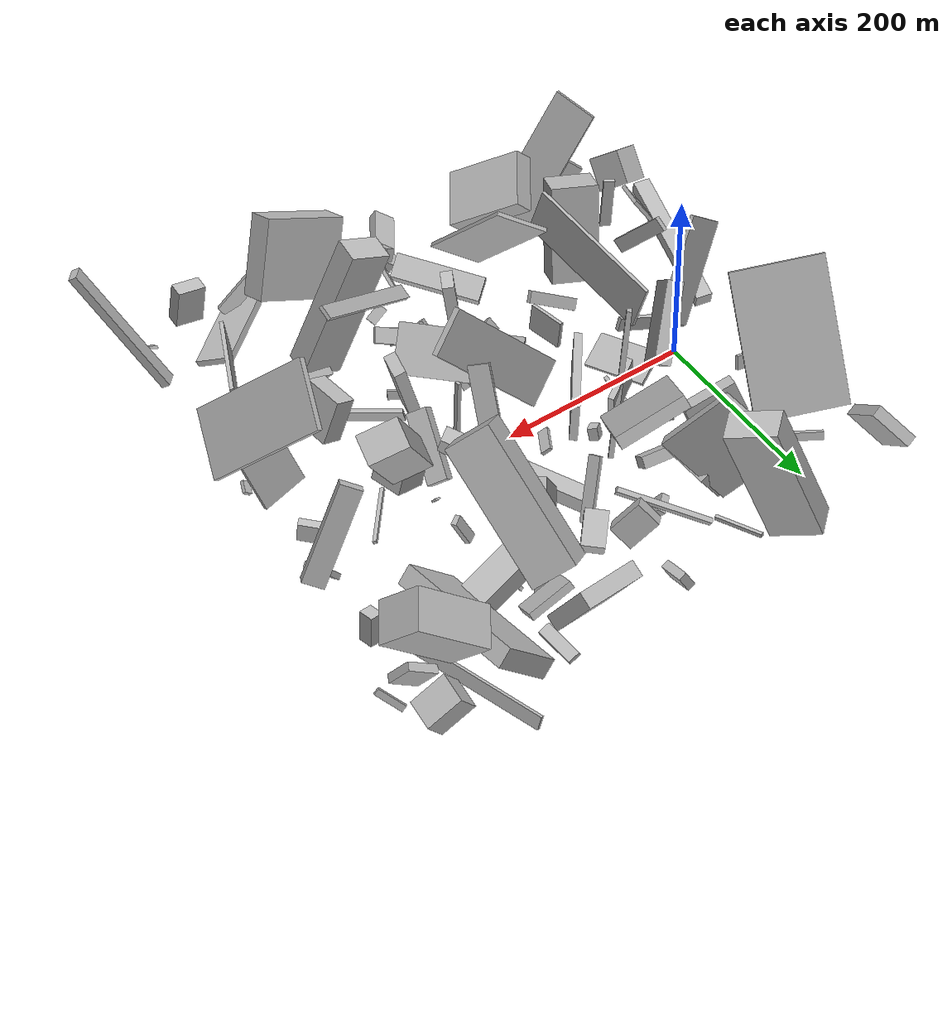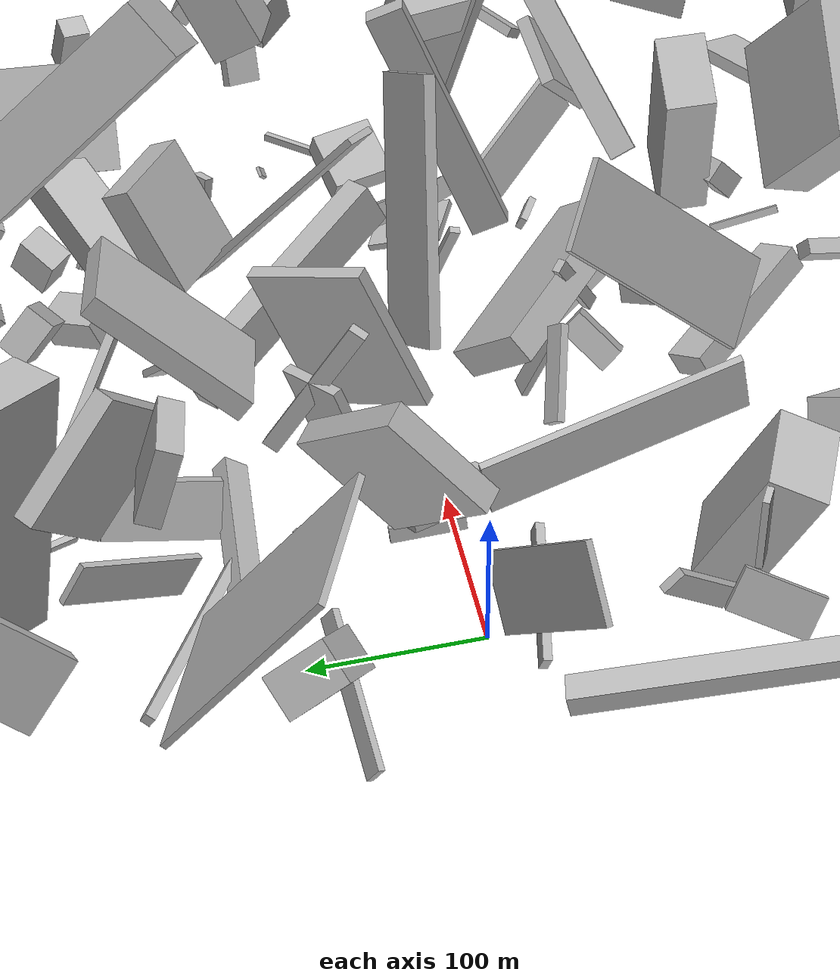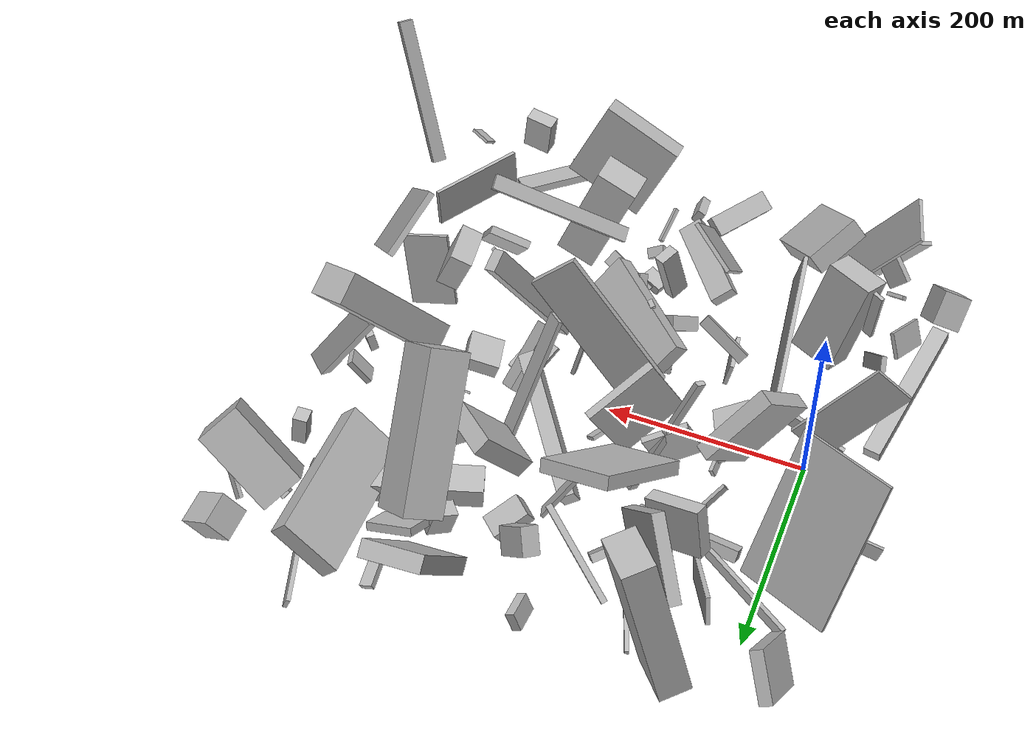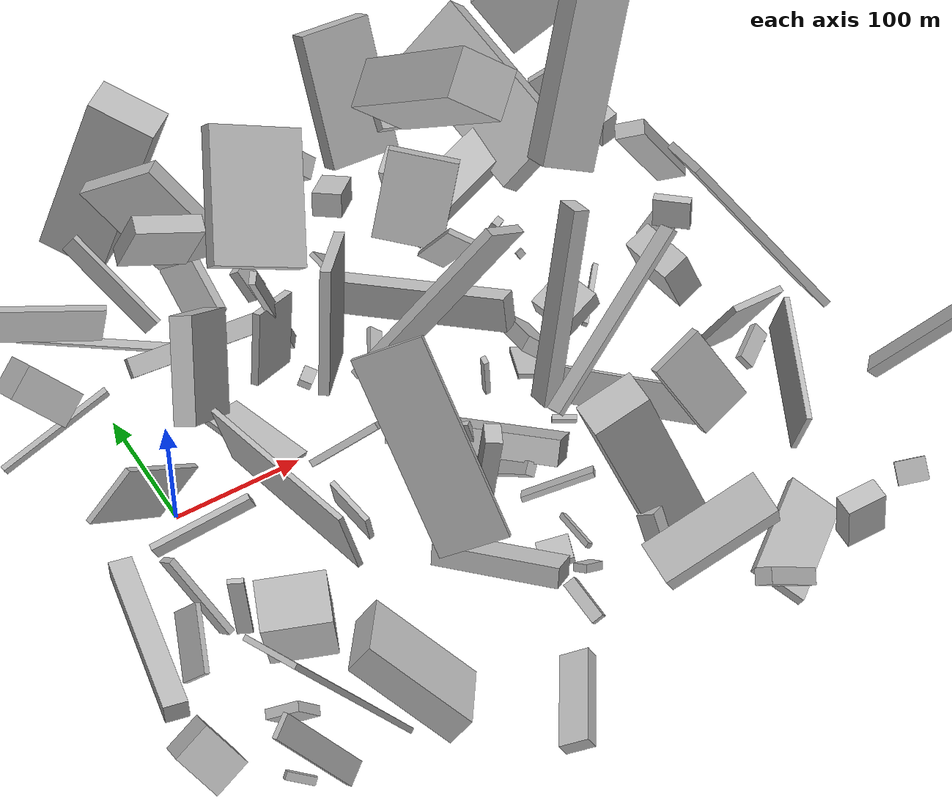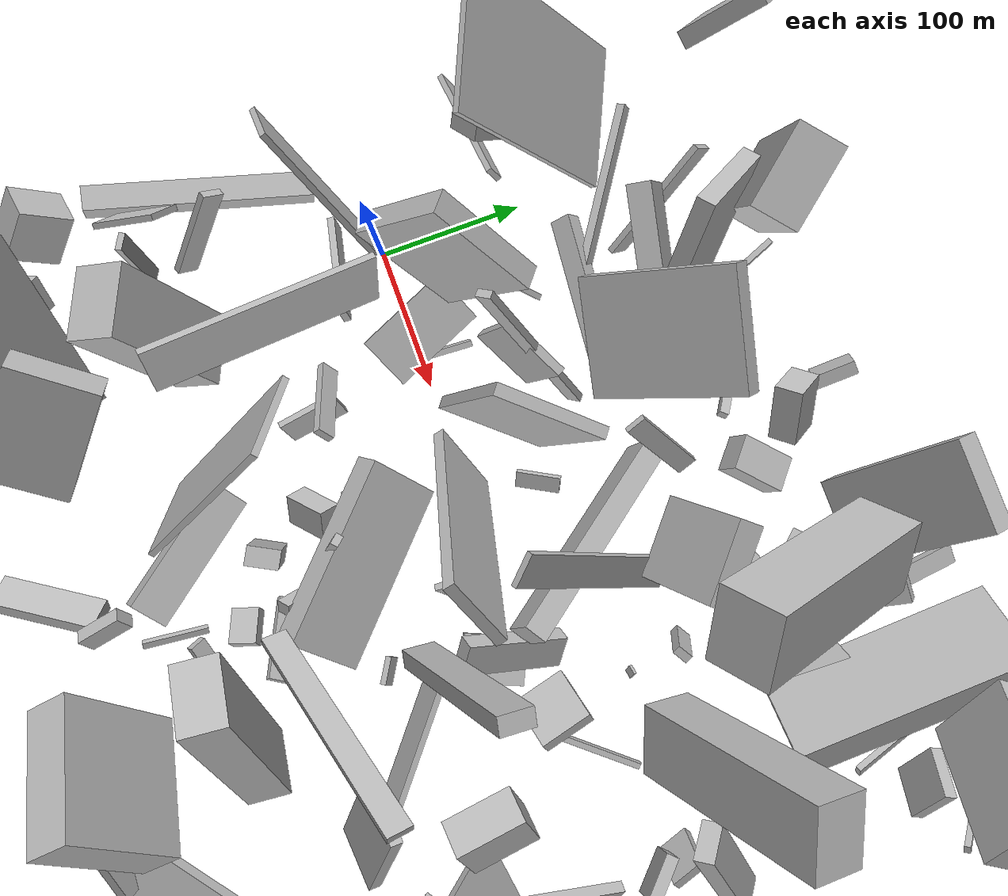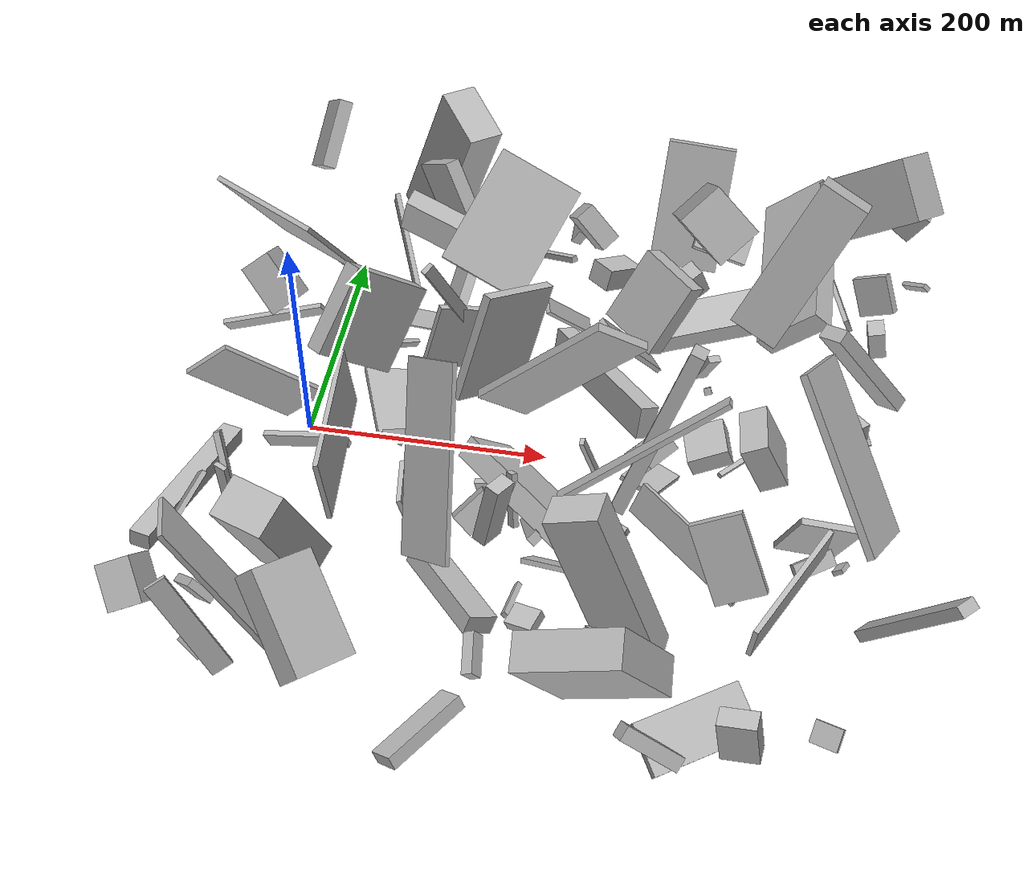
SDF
<sdf version="1.6">
 <world name="default">
  <scene>
   <sky><clouds><speed>12</speed></clouds></sky>
   <ambient>0.4 0.4 0.4 1</ambient>
   <background>0.7 0.7 0.7 1</background>
   <shadows>1</shadows>
  </scene>
  <gravity>0 0 -9.8066</gravity>
  <magnetic_field>6e-06 2.3e-05 -4.2e-05</magnetic_field>
  <physics default="0" name="default_physics" type="ode">
   <ode>
    <solver>
     <type>quick</type>
     <iters>10</iters>
     <sor>1.0</sor>
     <use_dynamic_moi_rescaling>0</use_dynamic_moi_rescaling>
    </solver>
    <constraints>
     <cfm>0</cfm>
     <erp>0.2</erp>
     <contact_max_correcting_vel>100</contact_max_correcting_vel>
     <contact_surface_layer>0.001</contact_surface_layer>
    </constraints>
   </ode>
   <max_step_size>0.004</max_step_size>
   <real_time_factor>1</real_time_factor>
   <real_time_update_rate>250</real_time_update_rate>
  </physics>
  <light name="sun" type="directional">
   <pose>0 0 10 0 0 0</pose>
   <diffuse>0.8 0.8 0.8 1</diffuse>
   <specular>0.2 0.2 0.2 1</specular>
   <attenuation>
    <range>1000</range>
    <constant>0.9</constant>
    <linear>0.01</linear>
    <quadratic>0.001</quadratic>
   </attenuation>
   <direction>-0.5 0.1 -0.9</direction>
  </light>
  <model name="building_1">
   <static>0</static>
   <pose>27.211838515866162 124.84362103675117 20.59560615158851 -1.547520387654282 0.6648058775224808 -1.6527169528336136</pose>
   <link name="link">
    <gravity>0</gravity>
    <pose>0 0 51.5 0 0 0</pose>
    <collision name="collision"><geometry><box><size>15 12 103</size></box></geometry></collision>
    <visual name="visual">
     <cast_shadows>0</cast_shadows>
     <geometry><box><size>15 12 103</size></box></geometry>
     <material>
      <script>
       <uri>model://HANNAS_wall/materials/scripts</uri>
       <uri>model://HANNAS_wall/materials/textures</uri>
       <name>vrc/HANNAS_wall</name>
      </script>
     </material>
    </visual>
   </link>
  </model>
  <model name="building_2">
   <static>0</static>
   <pose>451.5624902986939 -33.32970941571944 102.76273283419845 -0.8259827345149581 -0.7592758096414747 2.2470498553428886</pose>
   <link name="link">
    <gravity>0</gravity>
    <pose>0 0 35.5 0 0 0</pose>
    <collision name="collision"><geometry><box><size>145 6 71</size></box></geometry></collision>
    <visual name="visual">
     <cast_shadows>0</cast_shadows>
     <geometry><box><size>145 6 71</size></box></geometry>
     <material>
      <script>
       <uri>model://HANNAS_wall/materials/scripts</uri>
       <uri>model://HANNAS_wall/materials/textures</uri>
       <name>vrc/HANNAS_wall</name>
      </script>
     </material>
    </visual>
   </link>
  </model>
  <model name="building_3">
   <static>0</static>
   <pose>294.24459259865444 -49.984730838097406 99.87693806458475 -2.504968858752314 -1.0709866795299485 0.7755227535362518</pose>
   <link name="link">
    <gravity>0</gravity>
    <pose>0 0 11.0 0 0 0</pose>
    <collision name="collision"><geometry><box><size>150 12 22</size></box></geometry></collision>
    <visual name="visual">
     <cast_shadows>0</cast_shadows>
     <geometry><box><size>150 12 22</size></box></geometry>
     <material>
      <script>
       <uri>model://HANNAS_wall/materials/scripts</uri>
       <uri>model://HANNAS_wall/materials/textures</uri>
       <name>vrc/HANNAS_wall</name>
      </script>
     </material>
    </visual>
   </link>
  </model>
  <model name="building_4">
   <static>0</static>
   <pose>151.2767325008403 -107.09154220934064 32.48193512324727 0.9275128388393038 0.6493418718061549 1.8882977679449942</pose>
   <link name="link">
    <gravity>0</gravity>
    <pose>0 0 16.0 0 0 0</pose>
    <collision name="collision"><geometry><box><size>15 20 32</size></box></geometry></collision>
    <visual name="visual">
     <cast_shadows>0</cast_shadows>
     <geometry><box><size>15 20 32</size></box></geometry>
     <material>
      <script>
       <uri>model://HANNAS_wall/materials/scripts</uri>
       <uri>model://HANNAS_wall/materials/textures</uri>
       <name>vrc/HANNAS_wall</name>
      </script>
     </material>
    </visual>
   </link>
  </model>
  <model name="building_5">
   <static>0</static>
   <pose>296.1737670128903 -179.05190907568524 86.21473645385353 -2.9481805508152674 -1.1986294896747989 2.860380191356934</pose>
   <link name="link">
    <gravity>0</gravity>
    <pose>0 0 21.5 0 0 0</pose>
    <collision name="collision"><geometry><box><size>150 28 43</size></box></geometry></collision>
    <visual name="visual">
     <cast_shadows>0</cast_shadows>
     <geometry><box><size>150 28 43</size></box></geometry>
     <material>
      <script>
       <uri>model://HANNAS_wall/materials/scripts</uri>
       <uri>model://HANNAS_wall/materials/textures</uri>
       <name>vrc/HANNAS_wall</name>
      </script>
     </material>
    </visual>
   </link>
  </model>
  <model name="building_6">
   <static>0</static>
   <pose>71.12265748223888 -214.65724861649122 54.089847000162536 0.9755112662001612 -0.8217843174659927 -0.15030441125377775</pose>
   <link name="link">
    <gravity>0</gravity>
    <pose>0 0 29.0 0 0 0</pose>
    <collision name="collision"><geometry><box><size>22 85 58</size></box></geometry></collision>
    <visual name="visual">
     <cast_shadows>0</cast_shadows>
     <geometry><box><size>22 85 58</size></box></geometry>
     <material>
      <script>
       <uri>model://HANNAS_wall/materials/scripts</uri>
       <uri>model://HANNAS_wall/materials/textures</uri>
       <name>vrc/HANNAS_wall</name>
      </script>
     </material>
    </visual>
   </link>
  </model>
  <model name="building_7">
   <static>0</static>
   <pose>464.2543742640903 -189.53138008457 76.31035935655872 0.054750105578146066 0.5840906714023034 -0.7440478275020213</pose>
   <link name="link">
    <gravity>0</gravity>
    <pose>0 0 75.0 0 0 0</pose>
    <collision name="collision"><geometry><box><size>9 14 150</size></box></geometry></collision>
    <visual name="visual">
     <cast_shadows>0</cast_shadows>
     <geometry><box><size>9 14 150</size></box></geometry>
     <material>
      <script>
       <uri>model://HANNAS_wall/materials/scripts</uri>
       <uri>model://HANNAS_wall/materials/textures</uri>
       <name>vrc/HANNAS_wall</name>
      </script>
     </material>
    </visual>
   </link>
  </model>
  <model name="building_8">
   <static>0</static>
   <pose>232.10473915733326 58.1581610143995 36.5640051441885 2.403101025443369 -1.1771355175823404 1.3421056385738772</pose>
   <link name="link">
    <gravity>0</gravity>
    <pose>0 0 8.0 0 0 0</pose>
    <collision name="collision"><geometry><box><size>27 150 16</size></box></geometry></collision>
    <visual name="visual">
     <cast_shadows>0</cast_shadows>
     <geometry><box><size>27 150 16</size></box></geometry>
     <material>
      <script>
       <uri>model://HANNAS_wall/materials/scripts</uri>
       <uri>model://HANNAS_wall/materials/textures</uri>
       <name>vrc/HANNAS_wall</name>
      </script>
     </material>
    </visual>
   </link>
  </model>
  <model name="building_9">
   <static>0</static>
   <pose>402.8307953808595 -80.43801238531685 42.143537407230895 -2.058238575848827 -1.1165951587942737 -1.0037950295369915</pose>
   <link name="link">
    <gravity>0</gravity>
    <pose>0 0 24.5 0 0 0</pose>
    <collision name="collision"><geometry><box><size>76 5 49</size></box></geometry></collision>
    <visual name="visual">
     <cast_shadows>0</cast_shadows>
     <geometry><box><size>76 5 49</size></box></geometry>
     <material>
      <script>
       <uri>model://HANNAS_wall/materials/scripts</uri>
       <uri>model://HANNAS_wall/materials/textures</uri>
       <name>vrc/HANNAS_wall</name>
      </script>
     </material>
    </visual>
   </link>
  </model>
  <model name="building_10">
   <static>0</static>
   <pose>195.60094262296934 134.0635511246905 41.82748521522629 -2.147879168189077 -0.851470989063694 -2.389747482755872</pose>
   <link name="link">
    <gravity>0</gravity>
    <pose>0 0 7.0 0 0 0</pose>
    <collision name="collision"><geometry><box><size>65 4 14</size></box></geometry></collision>
    <visual name="visual">
     <cast_shadows>0</cast_shadows>
     <geometry><box><size>65 4 14</size></box></geometry>
     <material>
      <script>
       <uri>model://HANNAS_wall/materials/scripts</uri>
       <uri>model://HANNAS_wall/materials/textures</uri>
       <name>vrc/HANNAS_wall</name>
      </script>
     </material>
    </visual>
   </link>
  </model>
  <model name="building_11">
   <static>0</static>
   <pose>416.8292578173628 243.5296702717489 92.39256330262714 0.5658543221135247 -0.7652655764574674 2.1218722179549987</pose>
   <link name="link">
    <gravity>0</gravity>
    <pose>0 0 42.0 0 0 0</pose>
    <collision name="collision"><geometry><box><size>54 42 84</size></box></geometry></collision>
    <visual name="visual">
     <cast_shadows>0</cast_shadows>
     <geometry><box><size>54 42 84</size></box></geometry>
     <material>
      <script>
       <uri>model://HANNAS_wall/materials/scripts</uri>
       <uri>model://HANNAS_wall/materials/textures</uri>
       <name>vrc/HANNAS_wall</name>
      </script>
     </material>
    </visual>
   </link>
  </model>
  <model name="building_12">
   <static>0</static>
   <pose>406.99695888584796 -162.16269770112368 60.97939326974913 -0.11763524278981584 -0.15774184154037282 2.6952777827222993</pose>
   <link name="link">
    <gravity>0</gravity>
    <pose>0 0 19.0 0 0 0</pose>
    <collision name="collision"><geometry><box><size>4 103 38</size></box></geometry></collision>
    <visual name="visual">
     <cast_shadows>0</cast_shadows>
     <geometry><box><size>4 103 38</size></box></geometry>
     <material>
      <script>
       <uri>model://HANNAS_wall/materials/scripts</uri>
       <uri>model://HANNAS_wall/materials/textures</uri>
       <name>vrc/HANNAS_wall</name>
      </script>
     </material>
    </visual>
   </link>
  </model>
  <model name="building_13">
   <static>0</static>
   <pose>4.032316573456139 -31.386098392290506 27.423597168816624 2.808362640784029 -0.1357000118732573 1.4422339011119525</pose>
   <link name="link">
    <gravity>0</gravity>
    <pose>0 0 7.0 0 0 0</pose>
    <collision name="collision"><geometry><box><size>5 78 14</size></box></geometry></collision>
    <visual name="visual">
     <cast_shadows>0</cast_shadows>
     <geometry><box><size>5 78 14</size></box></geometry>
     <material>
      <script>
       <uri>model://HANNAS_wall/materials/scripts</uri>
       <uri>model://HANNAS_wall/materials/textures</uri>
       <name>vrc/HANNAS_wall</name>
      </script>
     </material>
    </visual>
   </link>
  </model>
  <model name="building_14">
   <static>0</static>
   <pose>189.72356766771176 45.76060640057053 27.33941011086246 -0.6595167242699409 0.06033873190293916 -2.0890858583591183</pose>
   <link name="link">
    <gravity>0</gravity>
    <pose>0 0 2.0 0 0 0</pose>
    <collision name="collision"><geometry><box><size>29 11 4</size></box></geometry></collision>
    <visual name="visual">
     <cast_shadows>0</cast_shadows>
     <geometry><box><size>29 11 4</size></box></geometry>
     <material>
      <script>
       <uri>model://HANNAS_wall/materials/scripts</uri>
       <uri>model://HANNAS_wall/materials/textures</uri>
       <name>vrc/HANNAS_wall</name>
      </script>
     </material>
    </visual>
   </link>
  </model>
  <model name="building_15">
   <static>0</static>
   <pose>83.05421869000531 -55.668051343389344 68.76536428135091 -0.9567382481227157 0.5513022646672949 -1.4916707012942982</pose>
   <link name="link">
    <gravity>0</gravity>
    <pose>0 0 27.0 0 0 0</pose>
    <collision name="collision"><geometry><box><size>5 12 54</size></box></geometry></collision>
    <visual name="visual">
     <cast_shadows>0</cast_shadows>
     <geometry><box><size>5 12 54</size></box></geometry>
     <material>
      <script>
       <uri>model://HANNAS_wall/materials/scripts</uri>
       <uri>model://HANNAS_wall/materials/textures</uri>
       <name>vrc/HANNAS_wall</name>
      </script>
     </material>
    </visual>
   </link>
  </model>
  <model name="building_16">
   <static>0</static>
   <pose>273.23977602309094 139.9273542329337 23.044295355234613 1.4812137355629744 -0.1765723079849566 1.9365967682955836</pose>
   <link name="link">
    <gravity>0</gravity>
    <pose>0 0 71.0 0 0 0</pose>
    <collision name="collision"><geometry><box><size>34 20 142</size></box></geometry></collision>
    <visual name="visual">
     <cast_shadows>0</cast_shadows>
     <geometry><box><size>34 20 142</size></box></geometry>
     <material>
      <script>
       <uri>model://HANNAS_wall/materials/scripts</uri>
       <uri>model://HANNAS_wall/materials/textures</uri>
       <name>vrc/HANNAS_wall</name>
      </script>
     </material>
    </visual>
   </link>
  </model>
  <model name="building_17">
   <static>0</static>
   <pose>303.46732956016973 -29.11324415672587 16.94607264653463 -1.4899946266989361 0.39201506307398987 1.1509717508772095</pose>
   <link name="link">
    <gravity>0</gravity>
    <pose>0 0 16.0 0 0 0</pose>
    <collision name="collision"><geometry><box><size>44 4 32</size></box></geometry></collision>
    <visual name="visual">
     <cast_shadows>0</cast_shadows>
     <geometry><box><size>44 4 32</size></box></geometry>
     <material>
      <script>
       <uri>model://HANNAS_wall/materials/scripts</uri>
       <uri>model://HANNAS_wall/materials/textures</uri>
       <name>vrc/HANNAS_wall</name>
      </script>
     </material>
    </visual>
   </link>
  </model>
  <model name="building_18">
   <static>0</static>
   <pose>84.97278747398177 257.36663713131594 87.08300735864296 1.4387214611380104 0.3218519411959484 -0.8850641235483556</pose>
   <link name="link">
    <gravity>0</gravity>
    <pose>0 0 15.5 0 0 0</pose>
    <collision name="collision"><geometry><box><size>53 150 31</size></box></geometry></collision>
    <visual name="visual">
     <cast_shadows>0</cast_shadows>
     <geometry><box><size>53 150 31</size></box></geometry>
     <material>
      <script>
       <uri>model://HANNAS_wall/materials/scripts</uri>
       <uri>model://HANNAS_wall/materials/textures</uri>
       <name>vrc/HANNAS_wall</name>
      </script>
     </material>
    </visual>
   </link>
  </model>
  <model name="building_19">
   <static>0</static>
   <pose>141.00837942629929 49.57422062666369 15.017187842737936 0.7845919502717803 -1.170461509970943 -1.634879975746383</pose>
   <link name="link">
    <gravity>0</gravity>
    <pose>0 0 5.0 0 0 0</pose>
    <collision name="collision"><geometry><box><size>13 12 10</size></box></geometry></collision>
    <visual name="visual">
     <cast_shadows>0</cast_shadows>
     <geometry><box><size>13 12 10</size></box></geometry>
     <material>
      <script>
       <uri>model://HANNAS_wall/materials/scripts</uri>
       <uri>model://HANNAS_wall/materials/textures</uri>
       <name>vrc/HANNAS_wall</name>
      </script>
     </material>
    </visual>
   </link>
  </model>
  <model name="building_20">
   <static>0</static>
   <pose>-51.62002118880841 -147.30420112321517 71.76723108918968 -2.6759814854458868 0.5400792590107414 -0.12164570405082717</pose>
   <link name="link">
    <gravity>0</gravity>
    <pose>0 0 13.0 0 0 0</pose>
    <collision name="collision"><geometry><box><size>4 48 26</size></box></geometry></collision>
    <visual name="visual">
     <cast_shadows>0</cast_shadows>
     <geometry><box><size>4 48 26</size></box></geometry>
     <material>
      <script>
       <uri>model://HANNAS_wall/materials/scripts</uri>
       <uri>model://HANNAS_wall/materials/textures</uri>
       <name>vrc/HANNAS_wall</name>
      </script>
     </material>
    </visual>
   </link>
  </model>
  <model name="building_21">
   <static>0</static>
   <pose>389.71632752535083 133.66970002863138 43.86489777275679 -1.3807405792760494 -0.7611349221695618 -0.08310338159188514</pose>
   <link name="link">
    <gravity>0</gravity>
    <pose>0 0 75.0 0 0 0</pose>
    <collision name="collision"><geometry><box><size>64 21 150</size></box></geometry></collision>
    <visual name="visual">
     <cast_shadows>0</cast_shadows>
     <geometry><box><size>64 21 150</size></box></geometry>
     <material>
      <script>
       <uri>model://HANNAS_wall/materials/scripts</uri>
       <uri>model://HANNAS_wall/materials/textures</uri>
       <name>vrc/HANNAS_wall</name>
      </script>
     </material>
    </visual>
   </link>
  </model>
  <model name="building_22">
   <static>0</static>
   <pose>-33.438903712791856 -221.27981078544016 69.20277285872248 2.493848589270199 -0.34049098860665267 1.1289027266845415</pose>
   <link name="link">
    <gravity>0</gravity>
    <pose>0 0 11.5 0 0 0</pose>
    <collision name="collision"><geometry><box><size>7 27 23</size></box></geometry></collision>
    <visual name="visual">
     <cast_shadows>0</cast_shadows>
     <geometry><box><size>7 27 23</size></box></geometry>
     <material>
      <script>
       <uri>model://HANNAS_wall/materials/scripts</uri>
       <uri>model://HANNAS_wall/materials/textures</uri>
       <name>vrc/HANNAS_wall</name>
      </script>
     </material>
    </visual>
   </link>
  </model>
  <model name="building_23">
   <static>0</static>
   <pose>215.22700282867342 -67.97996047458827 29.768134644519385 -0.06448674257944507 -0.8016641945003186 0.8675040339189963</pose>
   <link name="link">
    <gravity>0</gravity>
    <pose>0 0 25.5 0 0 0</pose>
    <collision name="collision"><geometry><box><size>19 123 51</size></box></geometry></collision>
    <visual name="visual">
     <cast_shadows>0</cast_shadows>
     <geometry><box><size>19 123 51</size></box></geometry>
     <material>
      <script>
       <uri>model://HANNAS_wall/materials/scripts</uri>
       <uri>model://HANNAS_wall/materials/textures</uri>
       <name>vrc/HANNAS_wall</name>
      </script>
     </material>
    </visual>
   </link>
  </model>
  <model name="building_24">
   <static>0</static>
   <pose>-23.988614353842344 -247.6736132114047 50.9372792480067 1.1623830595055502 -0.36851839528940045 0.6105968302007813</pose>
   <link name="link">
    <gravity>0</gravity>
    <pose>0 0 2.0 0 0 0</pose>
    <collision name="collision"><geometry><box><size>18 91 4</size></box></geometry></collision>
    <visual name="visual">
     <cast_shadows>0</cast_shadows>
     <geometry><box><size>18 91 4</size></box></geometry>
     <material>
      <script>
       <uri>model://HANNAS_wall/materials/scripts</uri>
       <uri>model://HANNAS_wall/materials/textures</uri>
       <name>vrc/HANNAS_wall</name>
      </script>
     </material>
    </visual>
   </link>
  </model>
  <model name="building_25">
   <static>0</static>
   <pose>42.32099973623684 190.20169762942533 36.65370870657631 -0.5811033391158684 0.03302482739769521 -2.7255378760665137</pose>
   <link name="link">
    <gravity>0</gravity>
    <pose>0 0 13.0 0 0 0</pose>
    <collision name="collision"><geometry><box><size>4 88 26</size></box></geometry></collision>
    <visual name="visual">
     <cast_shadows>0</cast_shadows>
     <geometry><box><size>4 88 26</size></box></geometry>
     <material>
      <script>
       <uri>model://HANNAS_wall/materials/scripts</uri>
       <uri>model://HANNAS_wall/materials/textures</uri>
       <name>vrc/HANNAS_wall</name>
      </script>
     </material>
    </visual>
   </link>
  </model>
  <model name="building_26">
   <static>0</static>
   <pose>288.51709681685725 247.7140468754138 71.99900788396296 2.1292871702510303 -0.08231000794868061 -3.127319023408665</pose>
   <link name="link">
    <gravity>0</gravity>
    <pose>0 0 8.5 0 0 0</pose>
    <collision name="collision"><geometry><box><size>59 109 17</size></box></geometry></collision>
    <visual name="visual">
     <cast_shadows>0</cast_shadows>
     <geometry><box><size>59 109 17</size></box></geometry>
     <material>
      <script>
       <uri>model://HANNAS_wall/materials/scripts</uri>
       <uri>model://HANNAS_wall/materials/textures</uri>
       <name>vrc/HANNAS_wall</name>
      </script>
     </material>
    </visual>
   </link>
  </model>
  <model name="building_27">
   <static>0</static>
   <pose>96.98040695652026 125.89139262104311 29.235518303758862 -1.293808813341832 -0.9646231017432036 -0.298071392580266</pose>
   <link name="link">
    <gravity>0</gravity>
    <pose>0 0 33.0 0 0 0</pose>
    <collision name="collision"><geometry><box><size>33 9 66</size></box></geometry></collision>
    <visual name="visual">
     <cast_shadows>0</cast_shadows>
     <geometry><box><size>33 9 66</size></box></geometry>
     <material>
      <script>
       <uri>model://HANNAS_wall/materials/scripts</uri>
       <uri>model://HANNAS_wall/materials/textures</uri>
       <name>vrc/HANNAS_wall</name>
      </script>
     </material>
    </visual>
   </link>
  </model>
  <model name="building_28">
   <static>0</static>
   <pose>-43.13764614890716 239.63071238930215 77.45015815784313 0.5446072326882333 0.6648837696882882 2.156376845692104</pose>
   <link name="link">
    <gravity>0</gravity>
    <pose>0 0 30.0 0 0 0</pose>
    <collision name="collision"><geometry><box><size>46 12 60</size></box></geometry></collision>
    <visual name="visual">
     <cast_shadows>0</cast_shadows>
     <geometry><box><size>46 12 60</size></box></geometry>
     <material>
      <script>
       <uri>model://HANNAS_wall/materials/scripts</uri>
       <uri>model://HANNAS_wall/materials/textures</uri>
       <name>vrc/HANNAS_wall</name>
      </script>
     </material>
    </visual>
   </link>
  </model>
  <model name="building_29">
   <static>0</static>
   <pose>454.0077429927321 204.68704744817262 30.739054861482575 2.204588631740438 -0.9285156461910716 2.134644522257019</pose>
   <link name="link">
    <gravity>0</gravity>
    <pose>0 0 4.5 0 0 0</pose>
    <collision name="collision"><geometry><box><size>34 32 9</size></box></geometry></collision>
    <visual name="visual">
     <cast_shadows>0</cast_shadows>
     <geometry><box><size>34 32 9</size></box></geometry>
     <material>
      <script>
       <uri>model://HANNAS_wall/materials/scripts</uri>
       <uri>model://HANNAS_wall/materials/textures</uri>
       <name>vrc/HANNAS_wall</name>
      </script>
     </material>
    </visual>
   </link>
  </model>
  <model name="building_30">
   <static>0</static>
   <pose>-31.36417800949688 -239.15920118520944 8.774959442405294 2.479385753158873 0.7455972902719538 -2.5316493583746156</pose>
   <link name="link">
    <gravity>0</gravity>
    <pose>0 0 2.0 0 0 0</pose>
    <collision name="collision"><geometry><box><size>6 22 4</size></box></geometry></collision>
    <visual name="visual">
     <cast_shadows>0</cast_shadows>
     <geometry><box><size>6 22 4</size></box></geometry>
     <material>
      <script>
       <uri>model://HANNAS_wall/materials/scripts</uri>
       <uri>model://HANNAS_wall/materials/textures</uri>
       <name>vrc/HANNAS_wall</name>
      </script>
     </material>
    </visual>
   </link>
  </model>
  <model name="building_31">
   <static>0</static>
   <pose>388.17584803030763 -282.0164363616808 42.30422748387398 0.0023739043710750913 -0.13676317492188012 -0.08147370555343918</pose>
   <link name="link">
    <gravity>0</gravity>
    <pose>0 0 20.5 0 0 0</pose>
    <collision name="collision"><geometry><box><size>29 16 41</size></box></geometry></collision>
    <visual name="visual">
     <cast_shadows>0</cast_shadows>
     <geometry><box><size>29 16 41</size></box></geometry>
     <material>
      <script>
       <uri>model://HANNAS_wall/materials/scripts</uri>
       <uri>model://HANNAS_wall/materials/textures</uri>
       <name>vrc/HANNAS_wall</name>
      </script>
     </material>
    </visual>
   </link>
  </model>
  <model name="building_32">
   <static>0</static>
   <pose>79.35312764998125 166.8938118598502 101.69075439091338 2.296859094426095 -1.1434882126669177 -0.9613459225057436</pose>
   <link name="link">
    <gravity>0</gravity>
    <pose>0 0 7.5 0 0 0</pose>
    <collision name="collision"><geometry><box><size>47 54 15</size></box></geometry></collision>
    <visual name="visual">
     <cast_shadows>0</cast_shadows>
     <geometry><box><size>47 54 15</size></box></geometry>
     <material>
      <script>
       <uri>model://HANNAS_wall/materials/scripts</uri>
       <uri>model://HANNAS_wall/materials/textures</uri>
       <name>vrc/HANNAS_wall</name>
      </script>
     </material>
    </visual>
   </link>
  </model>
  <model name="building_33">
   <static>0</static>
   <pose>156.5583010689324 -182.6293961566376 40.918287389989466 0.15990444128582296 -0.5184925155050153 -2.519461892789466</pose>
   <link name="link">
    <gravity>0</gravity>
    <pose>0 0 7.5 0 0 0</pose>
    <collision name="collision"><geometry><box><size>25 91 15</size></box></geometry></collision>
    <visual name="visual">
     <cast_shadows>0</cast_shadows>
     <geometry><box><size>25 91 15</size></box></geometry>
     <material>
      <script>
       <uri>model://HANNAS_wall/materials/scripts</uri>
       <uri>model://HANNAS_wall/materials/textures</uri>
       <name>vrc/HANNAS_wall</name>
      </script>
     </material>
    </visual>
   </link>
  </model>
  <model name="building_34">
   <static>0</static>
   <pose>444.1072434119529 -83.28287669640736 8.211256930859381 0.43426534998078237 -0.7922267940661423 2.4507759026894695</pose>
   <link name="link">
    <gravity>0</gravity>
    <pose>0 0 4.5 0 0 0</pose>
    <collision name="collision"><geometry><box><size>4 13 9</size></box></geometry></collision>
    <visual name="visual">
     <cast_shadows>0</cast_shadows>
     <geometry><box><size>4 13 9</size></box></geometry>
     <material>
      <script>
       <uri>model://HANNAS_wall/materials/scripts</uri>
       <uri>model://HANNAS_wall/materials/textures</uri>
       <name>vrc/HANNAS_wall</name>
      </script>
     </material>
    </visual>
   </link>
  </model>
  <model name="building_35">
   <static>0</static>
   <pose>463.60658622659093 278.60507834026726 57.6219582870776 0.6228165064096014 0.16278671352645022 1.4988296016554796</pose>
   <link name="link">
    <gravity>0</gravity>
    <pose>0 0 14.5 0 0 0</pose>
    <collision name="collision"><geometry><box><size>31 40 29</size></box></geometry></collision>
    <visual name="visual">
     <cast_shadows>0</cast_shadows>
     <geometry><box><size>31 40 29</size></box></geometry>
     <material>
      <script>
       <uri>model://HANNAS_wall/materials/scripts</uri>
       <uri>model://HANNAS_wall/materials/textures</uri>
       <name>vrc/HANNAS_wall</name>
      </script>
     </material>
    </visual>
   </link>
  </model>
  <model name="building_36">
   <static>0</static>
   <pose>-34.790450023955835 129.15812561405238 105.30588008723132 -2.1561440324514187 -0.09839569707197562 2.7145770878911963</pose>
   <link name="link">
    <gravity>0</gravity>
    <pose>0 0 2.0 0 0 0</pose>
    <collision name="collision"><geometry><box><size>94 150 4</size></box></geometry></collision>
    <visual name="visual">
     <cast_shadows>0</cast_shadows>
     <geometry><box><size>94 150 4</size></box></geometry>
     <material>
      <script>
       <uri>model://HANNAS_wall/materials/scripts</uri>
       <uri>model://HANNAS_wall/materials/textures</uri>
       <name>vrc/HANNAS_wall</name>
      </script>
     </material>
    </visual>
   </link>
  </model>
  <model name="building_37">
   <static>0</static>
   <pose>231.70824100440421 -130.868606887137 110.27158323949004 -0.9553997217885196 -0.44876100926736806 -1.5043587718758642</pose>
   <link name="link">
    <gravity>0</gravity>
    <pose>0 0 74.0 0 0 0</pose>
    <collision name="collision"><geometry><box><size>15 4 148</size></box></geometry></collision>
    <visual name="visual">
     <cast_shadows>0</cast_shadows>
     <geometry><box><size>15 4 148</size></box></geometry>
     <material>
      <script>
       <uri>model://HANNAS_wall/materials/scripts</uri>
       <uri>model://HANNAS_wall/materials/textures</uri>
       <name>vrc/HANNAS_wall</name>
      </script>
     </material>
    </visual>
   </link>
  </model>
  <model name="building_38">
   <static>0</static>
   <pose>211.22124045199027 -169.43228697006796 10.54079574492289 -2.9163793306872097 0.15634803066473366 -1.8960968574811505</pose>
   <link name="link">
    <gravity>0</gravity>
    <pose>0 0 4.5 0 0 0</pose>
    <collision name="collision"><geometry><box><size>19 24 9</size></box></geometry></collision>
    <visual name="visual">
     <cast_shadows>0</cast_shadows>
     <geometry><box><size>19 24 9</size></box></geometry>
     <material>
      <script>
       <uri>model://HANNAS_wall/materials/scripts</uri>
       <uri>model://HANNAS_wall/materials/textures</uri>
       <name>vrc/HANNAS_wall</name>
      </script>
     </material>
    </visual>
   </link>
  </model>
  <model name="building_39">
   <static>0</static>
   <pose>53.52100733027267 -84.36913834237176 68.20634369231799 0.1604917648877754 -0.1971734970545488 -1.4462767649290929</pose>
   <link name="link">
    <gravity>0</gravity>
    <pose>0 0 25.0 0 0 0</pose>
    <collision name="collision"><geometry><box><size>150 4 50</size></box></geometry></collision>
    <visual name="visual">
     <cast_shadows>0</cast_shadows>
     <geometry><box><size>150 4 50</size></box></geometry>
     <material>
      <script>
       <uri>model://HANNAS_wall/materials/scripts</uri>
       <uri>model://HANNAS_wall/materials/textures</uri>
       <name>vrc/HANNAS_wall</name>
      </script>
     </material>
    </visual>
   </link>
  </model>
  <model name="building_40">
   <static>0</static>
   <pose>352.4079281810323 -256.39441332288607 22.175360631776467 -0.4700656475528027 -0.053017605093378724 -2.500384729446948</pose>
   <link name="link">
    <gravity>0</gravity>
    <pose>0 0 3.5 0 0 0</pose>
    <collision name="collision"><geometry><box><size>88 41 7</size></box></geometry></collision>
    <visual name="visual">
     <cast_shadows>0</cast_shadows>
     <geometry><box><size>88 41 7</size></box></geometry>
     <material>
      <script>
       <uri>model://HANNAS_wall/materials/scripts</uri>
       <uri>model://HANNAS_wall/materials/textures</uri>
       <name>vrc/HANNAS_wall</name>
      </script>
     </material>
    </visual>
   </link>
  </model>
  <model name="building_41">
   <static>0</static>
   <pose>271.79682091670065 -207.1673770442826 26.632484901811797 -0.5803751985641832 0.32184685981914457 0.4581546008265512</pose>
   <link name="link">
    <gravity>0</gravity>
    <pose>0 0 10.5 0 0 0</pose>
    <collision name="collision"><geometry><box><size>13 14 21</size></box></geometry></collision>
    <visual name="visual">
     <cast_shadows>0</cast_shadows>
     <geometry><box><size>13 14 21</size></box></geometry>
     <material>
      <script>
       <uri>model://HANNAS_wall/materials/scripts</uri>
       <uri>model://HANNAS_wall/materials/textures</uri>
       <name>vrc/HANNAS_wall</name>
      </script>
     </material>
    </visual>
   </link>
  </model>
  <model name="building_42">
   <static>0</static>
   <pose>72.9918413976733 217.41684875379514 64.78037617015212 -0.16485084925485993 -0.8970367250918753 2.374388210322944</pose>
   <link name="link">
    <gravity>0</gravity>
    <pose>0 0 40.0 0 0 0</pose>
    <collision name="collision"><geometry><box><size>89 12 80</size></box></geometry></collision>
    <visual name="visual">
     <cast_shadows>0</cast_shadows>
     <geometry><box><size>89 12 80</size></box></geometry>
     <material>
      <script>
       <uri>model://HANNAS_wall/materials/scripts</uri>
       <uri>model://HANNAS_wall/materials/textures</uri>
       <name>vrc/HANNAS_wall</name>
      </script>
     </material>
    </visual>
   </link>
  </model>
  <model name="building_43">
   <static>0</static>
   <pose>139.52620380761385 -177.46917326616574 73.8988709648814 0.5563743474202348 -0.47791918308489767 -2.4012192454692083</pose>
   <link name="link">
    <gravity>0</gravity>
    <pose>0 0 75.0 0 0 0</pose>
    <collision name="collision"><geometry><box><size>4 53 150</size></box></geometry></collision>
    <visual name="visual">
     <cast_shadows>0</cast_shadows>
     <geometry><box><size>4 53 150</size></box></geometry>
     <material>
      <script>
       <uri>model://HANNAS_wall/materials/scripts</uri>
       <uri>model://HANNAS_wall/materials/textures</uri>
       <name>vrc/HANNAS_wall</name>
      </script>
     </material>
    </visual>
   </link>
  </model>
  <model name="building_44">
   <static>0</static>
   <pose>330.58878416692005 157.36615829399304 116.91532928834073 0.7500658532514553 -0.6930999128301367 -1.4300089720736593</pose>
   <link name="link">
    <gravity>0</gravity>
    <pose>0 0 24.0 0 0 0</pose>
    <collision name="collision"><geometry><box><size>150 40 48</size></box></geometry></collision>
    <visual name="visual">
     <cast_shadows>0</cast_shadows>
     <geometry><box><size>150 40 48</size></box></geometry>
     <material>
      <script>
       <uri>model://HANNAS_wall/materials/scripts</uri>
       <uri>model://HANNAS_wall/materials/textures</uri>
       <name>vrc/HANNAS_wall</name>
      </script>
     </material>
    </visual>
   </link>
  </model>
  <model name="building_45">
   <static>0</static>
   <pose>358.4368357552486 58.783996890516654 119.26855861125827 -0.3964755303602403 -0.4998448841902186 -1.7092407873880577</pose>
   <link name="link">
    <gravity>0</gravity>
    <pose>0 0 65.5 0 0 0</pose>
    <collision name="collision"><geometry><box><size>30 41 131</size></box></geometry></collision>
    <visual name="visual">
     <cast_shadows>0</cast_shadows>
     <geometry><box><size>30 41 131</size></box></geometry>
     <material>
      <script>
       <uri>model://HANNAS_wall/materials/scripts</uri>
       <uri>model://HANNAS_wall/materials/textures</uri>
       <name>vrc/HANNAS_wall</name>
      </script>
     </material>
    </visual>
   </link>
  </model>
  <model name="building_46">
   <static>0</static>
   <pose>150.23389417628954 161.74658379469804 15.721502129324408 2.1711968290938537 -0.15469858587282928 -2.413586390002391</pose>
   <link name="link">
    <gravity>0</gravity>
    <pose>0 0 4.0 0 0 0</pose>
    <collision name="collision"><geometry><box><size>20 28 8</size></box></geometry></collision>
    <visual name="visual">
     <cast_shadows>0</cast_shadows>
     <geometry><box><size>20 28 8</size></box></geometry>
     <material>
      <script>
       <uri>model://HANNAS_wall/materials/scripts</uri>
       <uri>model://HANNAS_wall/materials/textures</uri>
       <name>vrc/HANNAS_wall</name>
      </script>
     </material>
    </visual>
   </link>
  </model>
  <model name="building_47">
   <static>0</static>
   <pose>450.0305349884567 71.1932667982949 84.54379186134086 2.0343437883383646 -0.3817693499564903 -0.6717882274566818</pose>
   <link name="link">
    <gravity>0</gravity>
    <pose>0 0 6.0 0 0 0</pose>
    <collision name="collision"><geometry><box><size>23 103 12</size></box></geometry></collision>
    <visual name="visual">
     <cast_shadows>0</cast_shadows>
     <geometry><box><size>23 103 12</size></box></geometry>
     <material>
      <script>
       <uri>model://HANNAS_wall/materials/scripts</uri>
       <uri>model://HANNAS_wall/materials/textures</uri>
       <name>vrc/HANNAS_wall</name>
      </script>
     </material>
    </visual>
   </link>
  </model>
  <model name="building_48">
   <static>0</static>
   <pose>68.76633309982198 58.637748287891405 71.99944346733771 0.808965368325688 -0.17344585661524106 -0.6697018377091865</pose>
   <link name="link">
    <gravity>0</gravity>
    <pose>0 0 40.5 0 0 0</pose>
    <collision name="collision"><geometry><box><size>16 76 81</size></box></geometry></collision>
    <visual name="visual">
     <cast_shadows>0</cast_shadows>
     <geometry><box><size>16 76 81</size></box></geometry>
     <material>
      <script>
       <uri>model://HANNAS_wall/materials/scripts</uri>
       <uri>model://HANNAS_wall/materials/textures</uri>
       <name>vrc/HANNAS_wall</name>
      </script>
     </material>
    </visual>
   </link>
  </model>
  <model name="building_49">
   <static>0</static>
   <pose>271.40045511477166 -88.16103460836834 29.90727332395401 1.2062929205773025 0.0011164917379262557 2.603946091683736</pose>
   <link name="link">
    <gravity>0</gravity>
    <pose>0 0 2.0 0 0 0</pose>
    <collision name="collision"><geometry><box><size>18 9 4</size></box></geometry></collision>
    <visual name="visual">
     <cast_shadows>0</cast_shadows>
     <geometry><box><size>18 9 4</size></box></geometry>
     <material>
      <script>
       <uri>model://HANNAS_wall/materials/scripts</uri>
       <uri>model://HANNAS_wall/materials/textures</uri>
       <name>vrc/HANNAS_wall</name>
      </script>
     </material>
    </visual>
   </link>
  </model>
  <model name="building_50">
   <static>0</static>
   <pose>334.7808868385342 4.534212224421221 27.12997090948223 -0.014332911424639331 0.3387687012999824 -2.9095213940368536</pose>
   <link name="link">
    <gravity>0</gravity>
    <pose>0 0 8.5 0 0 0</pose>
    <collision name="collision"><geometry><box><size>34 35 17</size></box></geometry></collision>
    <visual name="visual">
     <cast_shadows>0</cast_shadows>
     <geometry><box><size>34 35 17</size></box></geometry>
     <material>
      <script>
       <uri>model://HANNAS_wall/materials/scripts</uri>
       <uri>model://HANNAS_wall/materials/textures</uri>
       <name>vrc/HANNAS_wall</name>
      </script>
     </material>
    </visual>
   </link>
  </model>
  <model name="building_51">
   <static>0</static>
   <pose>20.596185199099708 -139.7845809331872 61.51076527808255 -2.958609365830133 -1.1809345818381236 -2.144928433061227</pose>
   <link name="link">
    <gravity>0</gravity>
    <pose>0 0 17.5 0 0 0</pose>
    <collision name="collision"><geometry><box><size>101 48 35</size></box></geometry></collision>
    <visual name="visual">
     <cast_shadows>0</cast_shadows>
     <geometry><box><size>101 48 35</size></box></geometry>
     <material>
      <script>
       <uri>model://HANNAS_wall/materials/scripts</uri>
       <uri>model://HANNAS_wall/materials/textures</uri>
       <name>vrc/HANNAS_wall</name>
      </script>
     </material>
    </visual>
   </link>
  </model>
  <model name="building_52">
   <static>0</static>
   <pose>-18.99928889842897 -143.60622361312394 50.80145640086499 0.0211187506406131 -0.057114989751775744 -0.49751936429781063</pose>
   <link name="link">
    <gravity>0</gravity>
    <pose>0 0 29.5 0 0 0</pose>
    <collision name="collision"><geometry><box><size>11 4 59</size></box></geometry></collision>
    <visual name="visual">
     <cast_shadows>0</cast_shadows>
     <geometry><box><size>11 4 59</size></box></geometry>
     <material>
      <script>
       <uri>model://HANNAS_wall/materials/scripts</uri>
       <uri>model://HANNAS_wall/materials/textures</uri>
       <name>vrc/HANNAS_wall</name>
      </script>
     </material>
    </visual>
   </link>
  </model>
  <model name="building_53">
   <static>0</static>
   <pose>435.4642515123036 171.59204197638638 23.577099028111945 -1.6464946011865962 1.17307289553291 0.2338949910907363</pose>
   <link name="link">
    <gravity>0</gravity>
    <pose>0 0 75.0 0 0 0</pose>
    <collision name="collision"><geometry><box><size>14 4 150</size></box></geometry></collision>
    <visual name="visual">
     <cast_shadows>0</cast_shadows>
     <geometry><box><size>14 4 150</size></box></geometry>
     <material>
      <script>
       <uri>model://HANNAS_wall/materials/scripts</uri>
       <uri>model://HANNAS_wall/materials/textures</uri>
       <name>vrc/HANNAS_wall</name>
      </script>
     </material>
    </visual>
   </link>
  </model>
  <model name="building_54">
   <static>0</static>
   <pose>-32.61557959311533 -105.49193620937025 57.450985099725955 1.752191349309527 -0.7153957137342511 -1.3581077333536864</pose>
   <link name="link">
    <gravity>0</gravity>
    <pose>0 0 2.5 0 0 0</pose>
    <collision name="collision"><geometry><box><size>15 67 5</size></box></geometry></collision>
    <visual name="visual">
     <cast_shadows>0</cast_shadows>
     <geometry><box><size>15 67 5</size></box></geometry>
     <material>
      <script>
       <uri>model://HANNAS_wall/materials/scripts</uri>
       <uri>model://HANNAS_wall/materials/textures</uri>
       <name>vrc/HANNAS_wall</name>
      </script>
     </material>
    </visual>
   </link>
  </model>
  <model name="building_55">
   <static>0</static>
   <pose>488.030205621601 222.92478944563948 33.953437064244476 -2.470871224340476 0.4406892318496096 -2.085179920491473</pose>
   <link name="link">
    <gravity>0</gravity>
    <pose>0 0 3.5 0 0 0</pose>
    <collision name="collision"><geometry><box><size>4 31 7</size></box></geometry></collision>
    <visual name="visual">
     <cast_shadows>0</cast_shadows>
     <geometry><box><size>4 31 7</size></box></geometry>
     <material>
      <script>
       <uri>model://HANNAS_wall/materials/scripts</uri>
       <uri>model://HANNAS_wall/materials/textures</uri>
       <name>vrc/HANNAS_wall</name>
      </script>
     </material>
    </visual>
   </link>
  </model>
  <model name="building_56">
   <static>0</static>
   <pose>67.44347050944498 80.49974629229358 34.4320454326143 2.5713431041130086 0.23385630113290617 -0.8094382751064944</pose>
   <link name="link">
    <gravity>0</gravity>
    <pose>0 0 3.0 0 0 0</pose>
    <collision name="collision"><geometry><box><size>4 28 6</size></box></geometry></collision>
    <visual name="visual">
     <cast_shadows>0</cast_shadows>
     <geometry><box><size>4 28 6</size></box></geometry>
     <material>
      <script>
       <uri>model://HANNAS_wall/materials/scripts</uri>
       <uri>model://HANNAS_wall/materials/textures</uri>
       <name>vrc/HANNAS_wall</name>
      </script>
     </material>
    </visual>
   </link>
  </model>
  <model name="building_57">
   <static>0</static>
   <pose>107.90102892496405 204.6540523699561 12.67512056473441 1.457628351146101 0.08680380921244835 -2.7818852063922774</pose>
   <link name="link">
    <gravity>0</gravity>
    <pose>0 0 25.5 0 0 0</pose>
    <collision name="collision"><geometry><box><size>4 4 51</size></box></geometry></collision>
    <visual name="visual">
     <cast_shadows>0</cast_shadows>
     <geometry><box><size>4 4 51</size></box></geometry>
     <material>
      <script>
       <uri>model://HANNAS_wall/materials/scripts</uri>
       <uri>model://HANNAS_wall/materials/textures</uri>
       <name>vrc/HANNAS_wall</name>
      </script>
     </material>
    </visual>
   </link>
  </model>
  <model name="building_58">
   <static>0</static>
   <pose>238.97013515039882 -28.918078815326687 39.19176165508438 -0.9558057048662019 -1.257790742474574 -2.2764212014989513</pose>
   <link name="link">
    <gravity>0</gravity>
    <pose>0 0 2.0 0 0 0</pose>
    <collision name="collision"><geometry><box><size>58 6 4</size></box></geometry></collision>
    <visual name="visual">
     <cast_shadows>0</cast_shadows>
     <geometry><box><size>58 6 4</size></box></geometry>
     <material>
      <script>
       <uri>model://HANNAS_wall/materials/scripts</uri>
       <uri>model://HANNAS_wall/materials/textures</uri>
       <name>vrc/HANNAS_wall</name>
      </script>
     </material>
    </visual>
   </link>
  </model>
  <model name="building_59">
   <static>0</static>
   <pose>434.2011043555487 39.41925418338519 49.13510480990416 -1.4959350499035675 -0.1114759689062145 -2.354700455167348</pose>
   <link name="link">
    <gravity>0</gravity>
    <pose>0 0 14.5 0 0 0</pose>
    <collision name="collision"><geometry><box><size>8 25 29</size></box></geometry></collision>
    <visual name="visual">
     <cast_shadows>0</cast_shadows>
     <geometry><box><size>8 25 29</size></box></geometry>
     <material>
      <script>
       <uri>model://HANNAS_wall/materials/scripts</uri>
       <uri>model://HANNAS_wall/materials/textures</uri>
       <name>vrc/HANNAS_wall</name>
      </script>
     </material>
    </visual>
   </link>
  </model>
  <model name="building_60">
   <static>0</static>
   <pose>286.40719822685685 183.9191403377549 29.562553637911765 -0.006280746125209856 1.2115017770538161 0.7149784664151897</pose>
   <link name="link">
    <gravity>0</gravity>
    <pose>0 0 12.0 0 0 0</pose>
    <collision name="collision"><geometry><box><size>27 17 24</size></box></geometry></collision>
    <visual name="visual">
     <cast_shadows>0</cast_shadows>
     <geometry><box><size>27 17 24</size></box></geometry>
     <material>
      <script>
       <uri>model://HANNAS_wall/materials/scripts</uri>
       <uri>model://HANNAS_wall/materials/textures</uri>
       <name>vrc/HANNAS_wall</name>
      </script>
     </material>
    </visual>
   </link>
  </model>
  <model name="building_61">
   <static>0</static>
   <pose>237.34879323292037 -251.63726569307426 68.15770006340229 1.1308885868970955 -0.38856822253865003 1.6409999260962251</pose>
   <link name="link">
    <gravity>0</gravity>
    <pose>0 0 43.5 0 0 0</pose>
    <collision name="collision"><geometry><box><size>30 82 87</size></box></geometry></collision>
    <visual name="visual">
     <cast_shadows>0</cast_shadows>
     <geometry><box><size>30 82 87</size></box></geometry>
     <material>
      <script>
       <uri>model://HANNAS_wall/materials/scripts</uri>
       <uri>model://HANNAS_wall/materials/textures</uri>
       <name>vrc/HANNAS_wall</name>
      </script>
     </material>
    </visual>
   </link>
  </model>
  <model name="building_62">
   <static>0</static>
   <pose>366.6909670272046 -52.76340911807071 98.61597034632122 -1.161271704039408 -0.015815327205832598 -1.4488958853950187</pose>
   <link name="link">
    <gravity>0</gravity>
    <pose>0 0 11.0 0 0 0</pose>
    <collision name="collision"><geometry><box><size>42 46 22</size></box></geometry></collision>
    <visual name="visual">
     <cast_shadows>0</cast_shadows>
     <geometry><box><size>42 46 22</size></box></geometry>
     <material>
      <script>
       <uri>model://HANNAS_wall/materials/scripts</uri>
       <uri>model://HANNAS_wall/materials/textures</uri>
       <name>vrc/HANNAS_wall</name>
      </script>
     </material>
    </visual>
   </link>
  </model>
  <model name="building_63">
   <static>0</static>
   <pose>206.97262448903263 -196.81174549598262 65.17810925115784 0.3550000420236389 -0.6277798004845948 2.8338128762108212</pose>
   <link name="link">
    <gravity>0</gravity>
    <pose>0 0 2.0 0 0 0</pose>
    <collision name="collision"><geometry><box><size>4 39 4</size></box></geometry></collision>
    <visual name="visual">
     <cast_shadows>0</cast_shadows>
     <geometry><box><size>4 39 4</size></box></geometry>
     <material>
      <script>
       <uri>model://HANNAS_wall/materials/scripts</uri>
       <uri>model://HANNAS_wall/materials/textures</uri>
       <name>vrc/HANNAS_wall</name>
      </script>
     </material>
    </visual>
   </link>
  </model>
  <model name="building_64">
   <static>0</static>
   <pose>222.08838502430828 185.42861370512395 47.41075051129518 1.477527022470772 0.4039514590555226 0.8278142265251733</pose>
   <link name="link">
    <gravity>0</gravity>
    <pose>0 0 11.5 0 0 0</pose>
    <collision name="collision"><geometry><box><size>37 19 23</size></box></geometry></collision>
    <visual name="visual">
     <cast_shadows>0</cast_shadows>
     <geometry><box><size>37 19 23</size></box></geometry>
     <material>
      <script>
       <uri>model://HANNAS_wall/materials/scripts</uri>
       <uri>model://HANNAS_wall/materials/textures</uri>
       <name>vrc/HANNAS_wall</name>
      </script>
     </material>
    </visual>
   </link>
  </model>
  <model name="building_65">
   <static>0</static>
   <pose>82.82462699988704 -23.415167155689495 33.172230103996895 -1.4183125812451378 0.36826387722169585 0.4335496712430147</pose>
   <link name="link">
    <gravity>0</gravity>
    <pose>0 0 33.0 0 0 0</pose>
    <collision name="collision"><geometry><box><size>37 4 66</size></box></geometry></collision>
    <visual name="visual">
     <cast_shadows>0</cast_shadows>
     <geometry><box><size>37 4 66</size></box></geometry>
     <material>
      <script>
       <uri>model://HANNAS_wall/materials/scripts</uri>
       <uri>model://HANNAS_wall/materials/textures</uri>
       <name>vrc/HANNAS_wall</name>
      </script>
     </material>
    </visual>
   </link>
  </model>
  <model name="building_66">
   <static>0</static>
   <pose>102.71853771917385 -98.78902849190894 28.674495690973558 1.5018786802452857 0.19321091670107152 -3.014211866778772</pose>
   <link name="link">
    <gravity>0</gravity>
    <pose>0 0 20.0 0 0 0</pose>
    <collision name="collision"><geometry><box><size>4 28 40</size></box></geometry></collision>
    <visual name="visual">
     <cast_shadows>0</cast_shadows>
     <geometry><box><size>4 28 40</size></box></geometry>
     <material>
      <script>
       <uri>model://HANNAS_wall/materials/scripts</uri>
       <uri>model://HANNAS_wall/materials/textures</uri>
       <name>vrc/HANNAS_wall</name>
      </script>
     </material>
    </visual>
   </link>
  </model>
  <model name="building_67">
   <static>0</static>
   <pose>444.25109653693187 57.44168018583974 18.01136337524584 1.9155181862564672 0.5853467923018043 0.5683786569325912</pose>
   <link name="link">
    <gravity>0</gravity>
    <pose>0 0 11.0 0 0 0</pose>
    <collision name="collision"><geometry><box><size>6 30 22</size></box></geometry></collision>
    <visual name="visual">
     <cast_shadows>0</cast_shadows>
     <geometry><box><size>6 30 22</size></box></geometry>
     <material>
      <script>
       <uri>model://HANNAS_wall/materials/scripts</uri>
       <uri>model://HANNAS_wall/materials/textures</uri>
       <name>vrc/HANNAS_wall</name>
      </script>
     </material>
    </visual>
   </link>
  </model>
  <model name="building_68">
   <static>0</static>
   <pose>341.9177270874682 223.93257778659287 50.424460887769186 1.0238179568962893 -0.9097442622794562 -1.1262920801764762</pose>
   <link name="link">
    <gravity>0</gravity>
    <pose>0 0 24.0 0 0 0</pose>
    <collision name="collision"><geometry><box><size>8 29 48</size></box></geometry></collision>
    <visual name="visual">
     <cast_shadows>0</cast_shadows>
     <geometry><box><size>8 29 48</size></box></geometry>
     <material>
      <script>
       <uri>model://HANNAS_wall/materials/scripts</uri>
       <uri>model://HANNAS_wall/materials/textures</uri>
       <name>vrc/HANNAS_wall</name>
      </script>
     </material>
    </visual>
   </link>
  </model>
  <model name="building_69">
   <static>0</static>
   <pose>192.2421681139625 -104.00955769435211 36.03912140032342 -0.251761611309171 -0.4033717813592329 -0.7676321221855453</pose>
   <link name="link">
    <gravity>0</gravity>
    <pose>0 0 22.5 0 0 0</pose>
    <collision name="collision"><geometry><box><size>8 5 45</size></box></geometry></collision>
    <visual name="visual">
     <cast_shadows>0</cast_shadows>
     <geometry><box><size>8 5 45</size></box></geometry>
     <material>
      <script>
       <uri>model://HANNAS_wall/materials/scripts</uri>
       <uri>model://HANNAS_wall/materials/textures</uri>
       <name>vrc/HANNAS_wall</name>
      </script>
     </material>
    </visual>
   </link>
  </model>
  <model name="building_70">
   <static>0</static>
   <pose>231.44367373727738 -141.68312131457205 38.93737303172151 0.6475548493387281 0.3440569011824349 2.765567348146191</pose>
   <link name="link">
    <gravity>0</gravity>
    <pose>0 0 2.0 0 0 0</pose>
    <collision name="collision"><geometry><box><size>54 16 4</size></box></geometry></collision>
    <visual name="visual">
     <cast_shadows>0</cast_shadows>
     <geometry><box><size>54 16 4</size></box></geometry>
     <material>
      <script>
       <uri>model://HANNAS_wall/materials/scripts</uri>
       <uri>model://HANNAS_wall/materials/textures</uri>
       <name>vrc/HANNAS_wall</name>
      </script>
     </material>
    </visual>
   </link>
  </model>
  <model name="building_71">
   <static>0</static>
   <pose>386.04567163815864 43.26257309591417 9.33497752631203 1.3700447597441505 -1.280143873589188 -0.5118796279820621</pose>
   <link name="link">
    <gravity>0</gravity>
    <pose>0 0 32.5 0 0 0</pose>
    <collision name="collision"><geometry><box><size>4 4 65</size></box></geometry></collision>
    <visual name="visual">
     <cast_shadows>0</cast_shadows>
     <geometry><box><size>4 4 65</size></box></geometry>
     <material>
      <script>
       <uri>model://HANNAS_wall/materials/scripts</uri>
       <uri>model://HANNAS_wall/materials/textures</uri>
       <name>vrc/HANNAS_wall</name>
      </script>
     </material>
    </visual>
   </link>
  </model>
  <model name="building_72">
   <static>0</static>
   <pose>107.80485841601073 52.60512732412543 40.702221575070155 0.14251063192580435 -0.35769439913745066 -2.6373142881999785</pose>
   <link name="link">
    <gravity>0</gravity>
    <pose>0 0 28.5 0 0 0</pose>
    <collision name="collision"><geometry><box><size>45 6 57</size></box></geometry></collision>
    <visual name="visual">
     <cast_shadows>0</cast_shadows>
     <geometry><box><size>45 6 57</size></box></geometry>
     <material>
      <script>
       <uri>model://HANNAS_wall/materials/scripts</uri>
       <uri>model://HANNAS_wall/materials/textures</uri>
       <name>vrc/HANNAS_wall</name>
      </script>
     </material>
    </visual>
   </link>
  </model>
  <model name="building_73">
   <static>0</static>
   <pose>81.88633004250379 15.090529780344768 6.604378635336076 -2.733438505283273 0.06903962189031715 1.5311451917707821</pose>
   <link name="link">
    <gravity>0</gravity>
    <pose>0 0 4.5 0 0 0</pose>
    <collision name="collision"><geometry><box><size>43 4 9</size></box></geometry></collision>
    <visual name="visual">
     <cast_shadows>0</cast_shadows>
     <geometry><box><size>43 4 9</size></box></geometry>
     <material>
      <script>
       <uri>model://HANNAS_wall/materials/scripts</uri>
       <uri>model://HANNAS_wall/materials/textures</uri>
       <name>vrc/HANNAS_wall</name>
      </script>
     </material>
    </visual>
   </link>
  </model>
  <model name="building_74">
   <static>0</static>
   <pose>-52.152636493005694 118.21560140817938 55.03077621839303 -0.8611458093660636 0.5357615483834969 -2.6861481253022954</pose>
   <link name="link">
    <gravity>0</gravity>
    <pose>0 0 19.5 0 0 0</pose>
    <collision name="collision"><geometry><box><size>27 46 39</size></box></geometry></collision>
    <visual name="visual">
     <cast_shadows>0</cast_shadows>
     <geometry><box><size>27 46 39</size></box></geometry>
     <material>
      <script>
       <uri>model://HANNAS_wall/materials/scripts</uri>
       <uri>model://HANNAS_wall/materials/textures</uri>
       <name>vrc/HANNAS_wall</name>
      </script>
     </material>
    </visual>
   </link>
  </model>
  <model name="building_75">
   <static>0</static>
   <pose>-1.7673661482716199 -227.58580943697183 78.25866569768206 0.4772249060061645 -1.0162520906707577 3.0437636651632474</pose>
   <link name="link">
    <gravity>0</gravity>
    <pose>0 0 2.0 0 0 0</pose>
    <collision name="collision"><geometry><box><size>150 46 4</size></box></geometry></collision>
    <visual name="visual">
     <cast_shadows>0</cast_shadows>
     <geometry><box><size>150 46 4</size></box></geometry>
     <material>
      <script>
       <uri>model://HANNAS_wall/materials/scripts</uri>
       <uri>model://HANNAS_wall/materials/textures</uri>
       <name>vrc/HANNAS_wall</name>
      </script>
     </material>
    </visual>
   </link>
  </model>
  <model name="building_76">
   <static>0</static>
   <pose>189.06002996847894 -255.59799531022213 48.349187107563466 -0.9935880676857135 0.9819943234889512 0.621025509494474</pose>
   <link name="link">
    <gravity>0</gravity>
    <pose>0 0 16.0 0 0 0</pose>
    <collision name="collision"><geometry><box><size>13 9 32</size></box></geometry></collision>
    <visual name="visual">
     <cast_shadows>0</cast_shadows>
     <geometry><box><size>13 9 32</size></box></geometry>
     <material>
      <script>
       <uri>model://HANNAS_wall/materials/scripts</uri>
       <uri>model://HANNAS_wall/materials/textures</uri>
       <name>vrc/HANNAS_wall</name>
      </script>
     </material>
    </visual>
   </link>
  </model>
  <model name="building_77">
   <static>0</static>
   <pose>327.91464452924936 257.8470444892898 29.72918924127206 0.35645613282899924 0.11067159667181674 1.667260493642915</pose>
   <link name="link">
    <gravity>0</gravity>
    <pose>0 0 3.0 0 0 0</pose>
    <collision name="collision"><geometry><box><size>42 13 6</size></box></geometry></collision>
    <visual name="visual">
     <cast_shadows>0</cast_shadows>
     <geometry><box><size>42 13 6</size></box></geometry>
     <material>
      <script>
       <uri>model://HANNAS_wall/materials/scripts</uri>
       <uri>model://HANNAS_wall/materials/textures</uri>
       <name>vrc/HANNAS_wall</name>
      </script>
     </material>
    </visual>
   </link>
  </model>
  <model name="building_78">
   <static>0</static>
   <pose>341.994458156311 -127.94241194552139 49.50814175912183 1.1271991036881075 0.5016728948662855 1.5076052010952161</pose>
   <link name="link">
    <gravity>0</gravity>
    <pose>0 0 21.0 0 0 0</pose>
    <collision name="collision"><geometry><box><size>8 67 42</size></box></geometry></collision>
    <visual name="visual">
     <cast_shadows>0</cast_shadows>
     <geometry><box><size>8 67 42</size></box></geometry>
     <material>
      <script>
       <uri>model://HANNAS_wall/materials/scripts</uri>
       <uri>model://HANNAS_wall/materials/textures</uri>
       <name>vrc/HANNAS_wall</name>
      </script>
     </material>
    </visual>
   </link>
  </model>
  <model name="building_79">
   <static>0</static>
   <pose>275.94293514254207 126.84279964261877 70.17331349876352 -0.2183586744905599 0.9572584227387579 -2.4484814201017806</pose>
   <link name="link">
    <gravity>0</gravity>
    <pose>0 0 9.5 0 0 0</pose>
    <collision name="collision"><geometry><box><size>68 54 19</size></box></geometry></collision>
    <visual name="visual">
     <cast_shadows>0</cast_shadows>
     <geometry><box><size>68 54 19</size></box></geometry>
     <material>
      <script>
       <uri>model://HANNAS_wall/materials/scripts</uri>
       <uri>model://HANNAS_wall/materials/textures</uri>
       <name>vrc/HANNAS_wall</name>
      </script>
     </material>
    </visual>
   </link>
  </model>
  <model name="building_80">
   <static>0</static>
   <pose>213.48026544232536 -9.585063800600958 112.58141839960278 1.197980970683055 -0.6442277371495926 -2.75570294474143</pose>
   <link name="link">
    <gravity>0</gravity>
    <pose>0 0 3.5 0 0 0</pose>
    <collision name="collision"><geometry><box><size>49 150 7</size></box></geometry></collision>
    <visual name="visual">
     <cast_shadows>0</cast_shadows>
     <geometry><box><size>49 150 7</size></box></geometry>
     <material>
      <script>
       <uri>model://HANNAS_wall/materials/scripts</uri>
       <uri>model://HANNAS_wall/materials/textures</uri>
       <name>vrc/HANNAS_wall</name>
      </script>
     </material>
    </visual>
   </link>
  </model>
  <model name="building_81">
   <static>0</static>
   <pose>-30.625178664796813 -25.581356299225394 75.20782083950819 1.264584412812941 -0.8062261999126138 -2.628145259986439</pose>
   <link name="link">
    <gravity>0</gravity>
    <pose>0 0 2.0 0 0 0</pose>
    <collision name="collision"><geometry><box><size>107 46 4</size></box></geometry></collision>
    <visual name="visual">
     <cast_shadows>0</cast_shadows>
     <geometry><box><size>107 46 4</size></box></geometry>
     <material>
      <script>
       <uri>model://HANNAS_wall/materials/scripts</uri>
       <uri>model://HANNAS_wall/materials/textures</uri>
       <name>vrc/HANNAS_wall</name>
      </script>
     </material>
    </visual>
   </link>
  </model>
  <model name="building_82">
   <static>0</static>
   <pose>174.725754224014 -254.4072317921211 14.957122017638545 1.6255308697621487 1.0283394916504893 -0.5349786949685507</pose>
   <link name="link">
    <gravity>0</gravity>
    <pose>0 0 35.5 0 0 0</pose>
    <collision name="collision"><geometry><box><size>11 22 71</size></box></geometry></collision>
    <visual name="visual">
     <cast_shadows>0</cast_shadows>
     <geometry><box><size>11 22 71</size></box></geometry>
     <material>
      <script>
       <uri>model://HANNAS_wall/materials/scripts</uri>
       <uri>model://HANNAS_wall/materials/textures</uri>
       <name>vrc/HANNAS_wall</name>
      </script>
     </material>
    </visual>
   </link>
  </model>
  <model name="building_83">
   <static>0</static>
   <pose>185.94633320558765 255.8588722026903 21.77946261189581 -0.2720184950783321 -0.4326846394324848 -3.031576782172444</pose>
   <link name="link">
    <gravity>0</gravity>
    <pose>0 0 9.5 0 0 0</pose>
    <collision name="collision"><geometry><box><size>9 28 19</size></box></geometry></collision>
    <visual name="visual">
     <cast_shadows>0</cast_shadows>
     <geometry><box><size>9 28 19</size></box></geometry>
     <material>
      <script>
       <uri>model://HANNAS_wall/materials/scripts</uri>
       <uri>model://HANNAS_wall/materials/textures</uri>
       <name>vrc/HANNAS_wall</name>
      </script>
     </material>
    </visual>
   </link>
  </model>
  <model name="building_84">
   <static>0</static>
   <pose>422.2808387372267 -99.49463448245533 40.6116519090982 -3.115267655966847 -0.8418671743150543 -0.9635419324984238</pose>
   <link name="link">
    <gravity>0</gravity>
    <pose>0 0 6.5 0 0 0</pose>
    <collision name="collision"><geometry><box><size>6 34 13</size></box></geometry></collision>
    <visual name="visual">
     <cast_shadows>0</cast_shadows>
     <geometry><box><size>6 34 13</size></box></geometry>
     <material>
      <script>
       <uri>model://HANNAS_wall/materials/scripts</uri>
       <uri>model://HANNAS_wall/materials/textures</uri>
       <name>vrc/HANNAS_wall</name>
      </script>
     </material>
    </visual>
   </link>
  </model>
  <model name="building_85">
   <static>0</static>
   <pose>329.0859739327484 -92.32635839745436 28.777644190415533 0.1683899883059004 -1.1006903584219994 0.7290993043597672</pose>
   <link name="link">
    <gravity>0</gravity>
    <pose>0 0 2.0 0 0 0</pose>
    <collision name="collision"><geometry><box><size>28 116 4</size></box></geometry></collision>
    <visual name="visual">
     <cast_shadows>0</cast_shadows>
     <geometry><box><size>28 116 4</size></box></geometry>
     <material>
      <script>
       <uri>model://HANNAS_wall/materials/scripts</uri>
       <uri>model://HANNAS_wall/materials/textures</uri>
       <name>vrc/HANNAS_wall</name>
      </script>
     </material>
    </visual>
   </link>
  </model>
  <model name="building_86">
   <static>0</static>
   <pose>458.08085024705304 153.85402493148436 38.75989848695116 1.6960527969855161 -0.15120436536011417 0.146612643767502</pose>
   <link name="link">
    <gravity>0</gravity>
    <pose>0 0 8.0 0 0 0</pose>
    <collision name="collision"><geometry><box><size>14 32 16</size></box></geometry></collision>
    <visual name="visual">
     <cast_shadows>0</cast_shadows>
     <geometry><box><size>14 32 16</size></box></geometry>
     <material>
      <script>
       <uri>model://HANNAS_wall/materials/scripts</uri>
       <uri>model://HANNAS_wall/materials/textures</uri>
       <name>vrc/HANNAS_wall</name>
      </script>
     </material>
    </visual>
   </link>
  </model>
  <model name="building_87">
   <static>0</static>
   <pose>-32.86441711774937 190.1938707427846 26.44671560554211 -1.6172885754348152 0.4678091854308495 -2.1797928584738213</pose>
   <link name="link">
    <gravity>0</gravity>
    <pose>0 0 63.5 0 0 0</pose>
    <collision name="collision"><geometry><box><size>6 8 127</size></box></geometry></collision>
    <visual name="visual">
     <cast_shadows>0</cast_shadows>
     <geometry><box><size>6 8 127</size></box></geometry>
     <material>
      <script>
       <uri>model://HANNAS_wall/materials/scripts</uri>
       <uri>model://HANNAS_wall/materials/textures</uri>
       <name>vrc/HANNAS_wall</name>
      </script>
     </material>
    </visual>
   </link>
  </model>
  <model name="building_88">
   <static>0</static>
   <pose>118.69150065528254 69.76391530249155 85.36246917185571 1.4788447602497083 -0.42300162483238635 0.9231729578356433</pose>
   <link name="link">
    <gravity>0</gravity>
    <pose>0 0 2.5 0 0 0</pose>
    <collision name="collision"><geometry><box><size>10 150 5</size></box></geometry></collision>
    <visual name="visual">
     <cast_shadows>0</cast_shadows>
     <geometry><box><size>10 150 5</size></box></geometry>
     <material>
      <script>
       <uri>model://HANNAS_wall/materials/scripts</uri>
       <uri>model://HANNAS_wall/materials/textures</uri>
       <name>vrc/HANNAS_wall</name>
      </script>
     </material>
    </visual>
   </link>
  </model>
  <model name="building_89">
   <static>0</static>
   <pose>177.22531751713828 72.9083396912305 68.82459112403205 -0.05352103570777426 -1.1495011306755223 0.9707315448586958</pose>
   <link name="link">
    <gravity>0</gravity>
    <pose>0 0 37.0 0 0 0</pose>
    <collision name="collision"><geometry><box><size>96 8 74</size></box></geometry></collision>
    <visual name="visual">
     <cast_shadows>0</cast_shadows>
     <geometry><box><size>96 8 74</size></box></geometry>
     <material>
      <script>
       <uri>model://HANNAS_wall/materials/scripts</uri>
       <uri>model://HANNAS_wall/materials/textures</uri>
       <name>vrc/HANNAS_wall</name>
      </script>
     </material>
    </visual>
   </link>
  </model>
  <model name="building_90">
   <static>0</static>
   <pose>158.1579143994467 189.054928060014 49.9644700900006 -1.7750568077831985 -0.449319681836518 -0.6195828181336045</pose>
   <link name="link">
    <gravity>0</gravity>
    <pose>0 0 3.0 0 0 0</pose>
    <collision name="collision"><geometry><box><size>100 5 6</size></box></geometry></collision>
    <visual name="visual">
     <cast_shadows>0</cast_shadows>
     <geometry><box><size>100 5 6</size></box></geometry>
     <material>
      <script>
       <uri>model://HANNAS_wall/materials/scripts</uri>
       <uri>model://HANNAS_wall/materials/textures</uri>
       <name>vrc/HANNAS_wall</name>
      </script>
     </material>
    </visual>
   </link>
  </model>
  <model name="building_91">
   <static>0</static>
   <pose>161.38988427390353 -73.72247070353369 48.53325780483509 2.758587881752873 0.05468483832564588 -3.0199234514219144</pose>
   <link name="link">
    <gravity>0</gravity>
    <pose>0 0 21.5 0 0 0</pose>
    <collision name="collision"><geometry><box><size>11 4 43</size></box></geometry></collision>
    <visual name="visual">
     <cast_shadows>0</cast_shadows>
     <geometry><box><size>11 4 43</size></box></geometry>
     <material>
      <script>
       <uri>model://HANNAS_wall/materials/scripts</uri>
       <uri>model://HANNAS_wall/materials/textures</uri>
       <name>vrc/HANNAS_wall</name>
      </script>
     </material>
    </visual>
   </link>
  </model>
  <model name="building_92">
   <static>0</static>
   <pose>309.35550460921473 167.88899180356663 8.380671464534867 1.0130619865007546 0.5254028331697879 -1.5727608972333516</pose>
   <link name="link">
    <gravity>0</gravity>
    <pose>0 0 2.0 0 0 0</pose>
    <collision name="collision"><geometry><box><size>4 4 4</size></box></geometry></collision>
    <visual name="visual">
     <cast_shadows>0</cast_shadows>
     <geometry><box><size>4 4 4</size></box></geometry>
     <material>
      <script>
       <uri>model://HANNAS_wall/materials/scripts</uri>
       <uri>model://HANNAS_wall/materials/textures</uri>
       <name>vrc/HANNAS_wall</name>
      </script>
     </material>
    </visual>
   </link>
  </model>
  <model name="building_93">
   <static>0</static>
   <pose>-71.49355847695021 -100.08738230089097 37.12211287204712 2.9384522079321074 0.01782125646541942 -0.20123767218373553</pose>
   <link name="link">
    <gravity>0</gravity>
    <pose>0 0 7.0 0 0 0</pose>
    <collision name="collision"><geometry><box><size>17 150 14</size></box></geometry></collision>
    <visual name="visual">
     <cast_shadows>0</cast_shadows>
     <geometry><box><size>17 150 14</size></box></geometry>
     <material>
      <script>
       <uri>model://HANNAS_wall/materials/scripts</uri>
       <uri>model://HANNAS_wall/materials/textures</uri>
       <name>vrc/HANNAS_wall</name>
      </script>
     </material>
    </visual>
   </link>
  </model>
  <model name="building_94">
   <static>0</static>
   <pose>283.73525203677684 -10.169564910157018 30.889718673247636 0.6731474356814889 -0.5486241060289208 2.4786299244538728</pose>
   <link name="link">
    <gravity>0</gravity>
    <pose>0 0 6.0 0 0 0</pose>
    <collision name="collision"><geometry><box><size>22 72 12</size></box></geometry></collision>
    <visual name="visual">
     <cast_shadows>0</cast_shadows>
     <geometry><box><size>22 72 12</size></box></geometry>
     <material>
      <script>
       <uri>model://HANNAS_wall/materials/scripts</uri>
       <uri>model://HANNAS_wall/materials/textures</uri>
       <name>vrc/HANNAS_wall</name>
      </script>
     </material>
    </visual>
   </link>
  </model>
  <model name="building_95">
   <static>0</static>
   <pose>145.82068911209223 144.636186152172 120.15369676182962 0.4654415264997497 -0.6195663160164998 1.0854979342396198</pose>
   <link name="link">
    <gravity>0</gravity>
    <pose>0 0 6.5 0 0 0</pose>
    <collision name="collision"><geometry><box><size>103 74 13</size></box></geometry></collision>
    <visual name="visual">
     <cast_shadows>0</cast_shadows>
     <geometry><box><size>103 74 13</size></box></geometry>
     <material>
      <script>
       <uri>model://HANNAS_wall/materials/scripts</uri>
       <uri>model://HANNAS_wall/materials/textures</uri>
       <name>vrc/HANNAS_wall</name>
      </script>
     </material>
    </visual>
   </link>
  </model>
  <model name="building_96">
   <static>0</static>
   <pose>-47.888662487139825 87.15075631761964 33.80443260184829 0.3407798950549913 0.36561130287804533 -1.3819163821565854</pose>
   <link name="link">
    <gravity>0</gravity>
    <pose>0 0 7.0 0 0 0</pose>
    <collision name="collision"><geometry><box><size>4 92 14</size></box></geometry></collision>
    <visual name="visual">
     <cast_shadows>0</cast_shadows>
     <geometry><box><size>4 92 14</size></box></geometry>
     <material>
      <script>
       <uri>model://HANNAS_wall/materials/scripts</uri>
       <uri>model://HANNAS_wall/materials/textures</uri>
       <name>vrc/HANNAS_wall</name>
      </script>
     </material>
    </visual>
   </link>
  </model>
  <model name="building_97">
   <static>0</static>
   <pose>-70.69006542204198 -207.27030940344122 46.896558258030495 -2.0587897314612382 -0.6648004941837123 2.1198549467754253</pose>
   <link name="link">
    <gravity>0</gravity>
    <pose>0 0 14.5 0 0 0</pose>
    <collision name="collision"><geometry><box><size>37 35 29</size></box></geometry></collision>
    <visual name="visual">
     <cast_shadows>0</cast_shadows>
     <geometry><box><size>37 35 29</size></box></geometry>
     <material>
      <script>
       <uri>model://HANNAS_wall/materials/scripts</uri>
       <uri>model://HANNAS_wall/materials/textures</uri>
       <name>vrc/HANNAS_wall</name>
      </script>
     </material>
    </visual>
   </link>
  </model>
  <model name="building_98">
   <static>0</static>
   <pose>267.70848827018693 50.96317548022255 79.30057892420272 1.1597895864254155 0.5248538966823828 -2.5904905921720047</pose>
   <link name="link">
    <gravity>0</gravity>
    <pose>0 0 11.0 0 0 0</pose>
    <collision name="collision"><geometry><box><size>4 150 22</size></box></geometry></collision>
    <visual name="visual">
     <cast_shadows>0</cast_shadows>
     <geometry><box><size>4 150 22</size></box></geometry>
     <material>
      <script>
       <uri>model://HANNAS_wall/materials/scripts</uri>
       <uri>model://HANNAS_wall/materials/textures</uri>
       <name>vrc/HANNAS_wall</name>
      </script>
     </material>
    </visual>
   </link>
  </model>
  <model name="building_99">
   <static>0</static>
   <pose>316.54324986823707 91.55514122751954 33.848182541903725 2.1229635791752615 1.1287828039693963 2.6298729679222537</pose>
   <link name="link">
    <gravity>0</gravity>
    <pose>0 0 5.5 0 0 0</pose>
    <collision name="collision"><geometry><box><size>31 6 11</size></box></geometry></collision>
    <visual name="visual">
     <cast_shadows>0</cast_shadows>
     <geometry><box><size>31 6 11</size></box></geometry>
     <material>
      <script>
       <uri>model://HANNAS_wall/materials/scripts</uri>
       <uri>model://HANNAS_wall/materials/textures</uri>
       <name>vrc/HANNAS_wall</name>
      </script>
     </material>
    </visual>
   </link>
  </model>
  <model name="building_100">
   <static>0</static>
   <pose>176.18305533981186 -123.31738800935597 80.34436978044897 1.6869275375073216 0.18216249238966006 1.0775338374267485</pose>
   <link name="link">
    <gravity>0</gravity>
    <pose>0 0 6.0 0 0 0</pose>
    <collision name="collision"><geometry><box><size>20 57 12</size></box></geometry></collision>
    <visual name="visual">
     <cast_shadows>0</cast_shadows>
     <geometry><box><size>20 57 12</size></box></geometry>
     <material>
      <script>
       <uri>model://HANNAS_wall/materials/scripts</uri>
       <uri>model://HANNAS_wall/materials/textures</uri>
       <name>vrc/HANNAS_wall</name>
      </script>
     </material>
    </visual>
   </link>
  </model>
  <model name="building_101">
   <static>0</static>
   <pose>209.02177003733578 -103.18053853936237 30.781513964689292 0.8318424227540473 0.506672211463721 -2.3811076379719562</pose>
   <link name="link">
    <gravity>0</gravity>
    <pose>0 0 4.0 0 0 0</pose>
    <collision name="collision"><geometry><box><size>10 80 8</size></box></geometry></collision>
    <visual name="visual">
     <cast_shadows>0</cast_shadows>
     <geometry><box><size>10 80 8</size></box></geometry>
     <material>
      <script>
       <uri>model://HANNAS_wall/materials/scripts</uri>
       <uri>model://HANNAS_wall/materials/textures</uri>
       <name>vrc/HANNAS_wall</name>
      </script>
     </material>
    </visual>
   </link>
  </model>
  <model name="building_102">
   <static>0</static>
   <pose>218.287985621732 -193.4230754101251 15.762856624234832 1.009334623695902 0.5438873555704841 0.1467503079865557</pose>
   <link name="link">
    <gravity>0</gravity>
    <pose>0 0 5.5 0 0 0</pose>
    <collision name="collision"><geometry><box><size>19 6 11</size></box></geometry></collision>
    <visual name="visual">
     <cast_shadows>0</cast_shadows>
     <geometry><box><size>19 6 11</size></box></geometry>
     <material>
      <script>
       <uri>model://HANNAS_wall/materials/scripts</uri>
       <uri>model://HANNAS_wall/materials/textures</uri>
       <name>vrc/HANNAS_wall</name>
      </script>
     </material>
    </visual>
   </link>
  </model>
  <model name="building_103">
   <static>0</static>
   <pose>444.019157252095 -269.938237149259 44.54112598562912 0.2527120676985192 -0.8266295470423468 -2.166506981419639</pose>
   <link name="link">
    <gravity>0</gravity>
    <pose>0 0 8.5 0 0 0</pose>
    <collision name="collision"><geometry><box><size>3 22 17</size></box></geometry></collision>
    <visual name="visual">
     <cast_shadows>0</cast_shadows>
     <geometry><box><size>3 22 17</size></box></geometry>
     <material>
      <script>
       <uri>model://HANNAS_wall/materials/scripts</uri>
       <uri>model://HANNAS_wall/materials/textures</uri>
       <name>vrc/HANNAS_wall</name>
      </script>
     </material>
    </visual>
   </link>
  </model>
  <model name="building_104">
   <static>0</static>
   <pose>322.79443040123584 56.79863771009217 41.81915705535729 1.169044218723882 0.5541787567962846 1.4986538288206737</pose>
   <link name="link">
    <gravity>0</gravity>
    <pose>0 0 3.0 0 0 0</pose>
    <collision name="collision"><geometry><box><size>2 6 6</size></box></geometry></collision>
    <visual name="visual">
     <cast_shadows>0</cast_shadows>
     <geometry><box><size>2 6 6</size></box></geometry>
     <material>
      <script>
       <uri>model://HANNAS_wall/materials/scripts</uri>
       <uri>model://HANNAS_wall/materials/textures</uri>
       <name>vrc/HANNAS_wall</name>
      </script>
     </material>
    </visual>
   </link>
  </model>
  <model name="building_105">
   <static>0</static>
   <pose>326.2573869036657 -289.7974567073326 41.01802617079099 -2.4168977768180353 0.6439787474479167 0.0035657010550376573</pose>
   <link name="link">
    <gravity>0</gravity>
    <pose>0 0 7.0 0 0 0</pose>
    <collision name="collision"><geometry><box><size>52 12 14</size></box></geometry></collision>
    <visual name="visual">
     <cast_shadows>0</cast_shadows>
     <geometry><box><size>52 12 14</size></box></geometry>
     <material>
      <script>
       <uri>model://HANNAS_wall/materials/scripts</uri>
       <uri>model://HANNAS_wall/materials/textures</uri>
       <name>vrc/HANNAS_wall</name>
      </script>
     </material>
    </visual>
   </link>
  </model>
  <model name="building_106">
   <static>0</static>
   <pose>201.94427849863584 217.95838084794013 63.50215327801072 0.8464450823743137 -0.4056093424704783 0.8082581175327345</pose>
   <link name="link">
    <gravity>0</gravity>
    <pose>0 0 13.5 0 0 0</pose>
    <collision name="collision"><geometry><box><size>18 37 27</size></box></geometry></collision>
    <visual name="visual">
     <cast_shadows>0</cast_shadows>
     <geometry><box><size>18 37 27</size></box></geometry>
     <material>
      <script>
       <uri>model://HANNAS_wall/materials/scripts</uri>
       <uri>model://HANNAS_wall/materials/textures</uri>
       <name>vrc/HANNAS_wall</name>
      </script>
     </material>
    </visual>
   </link>
  </model>
 </world>
</sdf>
